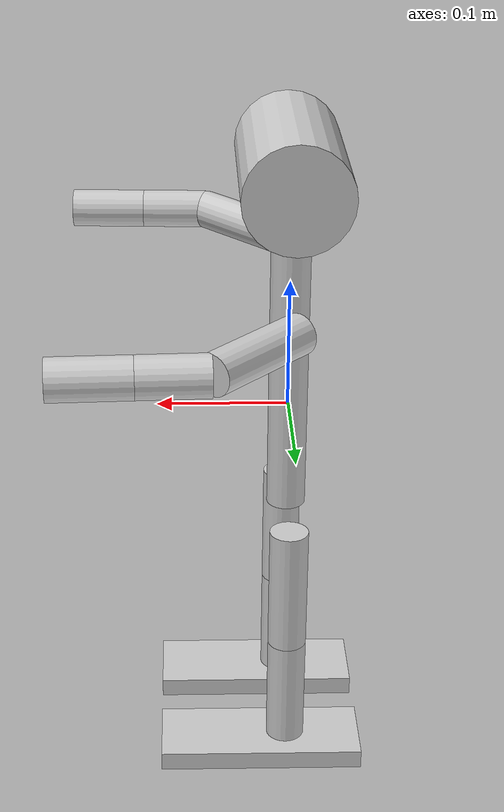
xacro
<?xml version="1.0" ?>
<robot name="NaoH25V32" xmlns:xacro="http://www.ros.org/wiki/xacro">
	<xacro:include filename="nao_visual_collisions.xacro"/>
	<xacro:include filename="nao_head.xacro"/>
	<xacro:include filename="nao_legs.xacro"/>
	<xacro:include filename="nao_torso.xacro"/>
	<xacro:include filename="nao_arms.xacro"/>
	<xacro:include filename="nao_sensors.xacro"/>
	<xacro:include filename="nao_fingers.xacro"/>
	<xacro:include filename="naoGazebo.xacro"/>
	<xacro:include filename="naoTransmission.xacro"/>
</robot>

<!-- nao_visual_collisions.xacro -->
<robot xmlns:xacro="http://www.ros.org/wiki/xacro">
	<xacro:property name="PI_2" value="1.57079632679"/>
	<xacro:property name="meshes_installed" value="false"/>
	<xacro:macro name="insert_visu_RFinger23_link">
		<xacro:unless value="${meshes_installed}"/>
		<xacro:if value="${meshes_installed}">
			<visual>
				<geometry>
					<mesh filename="package://nao_meshes/meshes/V32/RFinger23.dae" scale="0.1 0.1 0.1"/>
				</geometry>
				<origin rpy="0 0 0" xyz="0 0 0"/>
			</visual>
			<collision>
				<geometry>
					<mesh filename="package://nao_meshes/meshes/V32/RFinger23_0.10.stl" scale="0.1 0.1 0.1"/>
				</geometry>
				<origin rpy="0 0 0" xyz="0 0 0"/>
			</collision>
		</xacro:if>
	</xacro:macro>
	<xacro:macro name="insert_visu_LThigh">
		<xacro:unless value="${meshes_installed}">
			<visual>
				<geometry>
					<cylinder length="0.1" radius="0.015"/>
				</geometry>
				<origin rpy="0 0 0" xyz="0 0 -0.05"/>
				<material name="LightGrey"/>
			</visual>
			<collision>
				<geometry>
					<cylinder length="0.1" radius="0.015"/>
				</geometry>
				<origin rpy="0 0 0" xyz="0 0 -0.05"/>
			</collision>
		</xacro:unless>
		<xacro:if value="${meshes_installed}">
			<visual>
				<geometry>
					<mesh filename="package://nao_meshes/meshes/V32/LHipPitch.dae" scale="0.1 0.1 0.1"/>
				</geometry>
				<origin rpy="0 0 0" xyz="0 0 0"/>
			</visual>
			<collision>
				<geometry>
					<mesh filename="package://nao_meshes/meshes/V32/LHipPitch_0.10.stl" scale="0.1 0.1 0.1"/>
				</geometry>
				<origin rpy="0 0 0" xyz="0 0 0"/>
			</collision>
		</xacro:if>
	</xacro:macro>
	<xacro:macro name="insert_visu_RFinger13_link">
		<xacro:unless value="${meshes_installed}"/>
		<xacro:if value="${meshes_installed}">
			<visual>
				<geometry>
					<mesh filename="package://nao_meshes/meshes/V32/RFinger13.dae" scale="0.1 0.1 0.1"/>
				</geometry>
				<origin rpy="0 0 0" xyz="0 0 0"/>
			</visual>
			<collision>
				<geometry>
					<mesh filename="package://nao_meshes/meshes/V32/RFinger13_0.10.stl" scale="0.1 0.1 0.1"/>
				</geometry>
				<origin rpy="0 0 0" xyz="0 0 0"/>
			</collision>
		</xacro:if>
	</xacro:macro>
	<xacro:macro name="insert_visu_RThigh">
		<xacro:unless value="${meshes_installed}">
			<visual>
				<geometry>
					<cylinder length="0.1" radius="0.015"/>
				</geometry>
				<origin rpy="0 0 0" xyz="0 0 -0.05"/>
				<material name="LightGrey"/>
			</visual>
			<collision>
				<geometry>
					<cylinder length="0.1" radius="0.015"/>
				</geometry>
				<origin rpy="0 0 0" xyz="0 0 -0.05"/>
			</collision>
		</xacro:unless>
		<xacro:if value="${meshes_installed}">
			<visual>
				<geometry>
					<mesh filename="package://nao_meshes/meshes/V32/RHipPitch.dae" scale="0.1 0.1 0.1"/>
				</geometry>
				<origin rpy="0 0 0" xyz="0 0 0"/>
			</visual>
			<collision>
				<geometry>
					<mesh filename="package://nao_meshes/meshes/V32/RHipPitch_0.10.stl" scale="0.1 0.1 0.1"/>
				</geometry>
				<origin rpy="0 0 0" xyz="0 0 0"/>
			</collision>
		</xacro:if>
	</xacro:macro>
	<xacro:macro name="insert_visu_RFinger12_link">
		<xacro:unless value="${meshes_installed}"/>
		<xacro:if value="${meshes_installed}">
			<visual>
				<geometry>
					<mesh filename="package://nao_meshes/meshes/V32/RFinger12.dae" scale="0.1 0.1 0.1"/>
				</geometry>
				<origin rpy="0 0 0" xyz="0 0 0"/>
			</visual>
			<collision>
				<geometry>
					<mesh filename="package://nao_meshes/meshes/V32/RFinger12_0.10.stl" scale="0.1 0.1 0.1"/>
				</geometry>
				<origin rpy="0 0 0" xyz="0 0 0"/>
			</collision>
		</xacro:if>
	</xacro:macro>
	<xacro:macro name="insert_visu_LFinger21_link">
		<xacro:unless value="${meshes_installed}"/>
		<xacro:if value="${meshes_installed}">
			<visual>
				<geometry>
					<mesh filename="package://nao_meshes/meshes/V32/LFinger21.dae" scale="0.1 0.1 0.1"/>
				</geometry>
				<origin rpy="0 0 0" xyz="0 0 0"/>
			</visual>
			<collision>
				<geometry>
					<mesh filename="package://nao_meshes/meshes/V32/LFinger21_0.10.stl" scale="0.1 0.1 0.1"/>
				</geometry>
				<origin rpy="0 0 0" xyz="0 0 0"/>
			</collision>
		</xacro:if>
	</xacro:macro>
	<xacro:macro name="insert_visu_LFinger13_link">
		<xacro:unless value="${meshes_installed}"/>
		<xacro:if value="${meshes_installed}">
			<visual>
				<geometry>
					<mesh filename="package://nao_meshes/meshes/V32/LFinger13.dae" scale="0.1 0.1 0.1"/>
				</geometry>
				<origin rpy="0 0 0" xyz="0 0 0"/>
			</visual>
			<collision>
				<geometry>
					<mesh filename="package://nao_meshes/meshes/V32/LFinger13_0.10.stl" scale="0.1 0.1 0.1"/>
				</geometry>
				<origin rpy="0 0 0" xyz="0 0 0"/>
			</collision>
		</xacro:if>
	</xacro:macro>
	<xacro:macro name="insert_visu_LThumb1_link">
		<xacro:unless value="${meshes_installed}"/>
		<xacro:if value="${meshes_installed}">
			<visual>
				<geometry>
					<mesh filename="package://nao_meshes/meshes/V32/LThumb1.dae" scale="0.1 0.1 0.1"/>
				</geometry>
				<origin rpy="0 0 0" xyz="0 0 0"/>
			</visual>
			<collision>
				<geometry>
					<mesh filename="package://nao_meshes/meshes/V32/LThumb1_0.10.stl" scale="0.1 0.1 0.1"/>
				</geometry>
				<origin rpy="0 0 0" xyz="0 0 0"/>
			</collision>
		</xacro:if>
	</xacro:macro>
	<xacro:macro name="insert_visu_LFinger11_link">
		<xacro:unless value="${meshes_installed}"/>
		<xacro:if value="${meshes_installed}">
			<visual>
				<geometry>
					<mesh filename="package://nao_meshes/meshes/V32/LFinger11.dae" scale="0.1 0.1 0.1"/>
				</geometry>
				<origin rpy="0 0 0" xyz="0 0 0"/>
			</visual>
			<collision>
				<geometry>
					<mesh filename="package://nao_meshes/meshes/V32/LFinger11_0.10.stl" scale="0.1 0.1 0.1"/>
				</geometry>
				<origin rpy="0 0 0" xyz="0 0 0"/>
			</collision>
		</xacro:if>
	</xacro:macro>
	<xacro:macro name="insert_visu_RFinger22_link">
		<xacro:unless value="${meshes_installed}"/>
		<xacro:if value="${meshes_installed}">
			<visual>
				<geometry>
					<mesh filename="package://nao_meshes/meshes/V32/RFinger22.dae" scale="0.1 0.1 0.1"/>
				</geometry>
				<origin rpy="0 0 0" xyz="0 0 0"/>
			</visual>
			<collision>
				<geometry>
					<mesh filename="package://nao_meshes/meshes/V32/RFinger22_0.10.stl" scale="0.1 0.1 0.1"/>
				</geometry>
				<origin rpy="0 0 0" xyz="0 0 0"/>
			</collision>
		</xacro:if>
	</xacro:macro>
	<xacro:macro name="insert_visu_Head">
		<xacro:unless value="${meshes_installed}">
			<visual>
				<geometry>
					<cylinder length="0.14" radius="0.04"/>
				</geometry>
				<origin rpy="1.57079632679 0 0" xyz="0 0 0.058"/>
				<material name="LightGrey"/>
			</visual>
			<collision>
				<geometry>
					<cylinder length="0.14" radius="0.04"/>
				</geometry>
				<origin rpy="1.57079632679 0 0" xyz="0 0 0.058"/>
			</collision>
		</xacro:unless>
		<xacro:if value="${meshes_installed}">
			<visual>
				<geometry>
					<mesh filename="package://nao_meshes/meshes/V32/HeadPitch.dae" scale="0.1 0.1 0.1"/>
				</geometry>
				<origin rpy="0 0 0" xyz="0 0 0"/>
			</visual>
			<collision>
				<geometry>
					<mesh filename="package://nao_meshes/meshes/V32/HeadPitch_0.10.stl" scale="0.1 0.1 0.1"/>
				</geometry>
				<origin rpy="0 0 0" xyz="0 0 0"/>
			</collision>
		</xacro:if>
	</xacro:macro>
	<xacro:macro name="insert_visu_LFinger22_link">
		<xacro:unless value="${meshes_installed}"/>
		<xacro:if value="${meshes_installed}">
			<visual>
				<geometry>
					<mesh filename="package://nao_meshes/meshes/V32/LFinger22.dae" scale="0.1 0.1 0.1"/>
				</geometry>
				<origin rpy="0 0 0" xyz="0 0 0"/>
			</visual>
			<collision>
				<geometry>
					<mesh filename="package://nao_meshes/meshes/V32/LFinger22_0.10.stl" scale="0.1 0.1 0.1"/>
				</geometry>
				<origin rpy="0 0 0" xyz="0 0 0"/>
			</collision>
		</xacro:if>
	</xacro:macro>
	<xacro:macro name="insert_visu_RFinger21_link">
		<xacro:unless value="${meshes_installed}"/>
		<xacro:if value="${meshes_installed}">
			<visual>
				<geometry>
					<mesh filename="package://nao_meshes/meshes/V32/RFinger21.dae" scale="0.1 0.1 0.1"/>
				</geometry>
				<origin rpy="0 0 0" xyz="0 0 0"/>
			</visual>
			<collision>
				<geometry>
					<mesh filename="package://nao_meshes/meshes/V32/RFinger21_0.10.stl" scale="0.1 0.1 0.1"/>
				</geometry>
				<origin rpy="0 0 0" xyz="0 0 0"/>
			</collision>
		</xacro:if>
	</xacro:macro>
	<xacro:macro name="insert_visu_LBicep">
		<xacro:unless value="${meshes_installed}">
			<visual>
				<geometry>
					<cylinder length="0.09" radius="0.015"/>
				</geometry>
				<origin rpy="1.57079632679 0 1.57079632679" xyz="0.045 0 0"/>
				<material name="LightGrey"/>
			</visual>
			<collision>
				<geometry>
					<cylinder length="0.09" radius="0.015"/>
				</geometry>
				<origin rpy="1.57079632679 0 1.57079632679" xyz="0.045 0 0"/>
			</collision>
		</xacro:unless>
		<xacro:if value="${meshes_installed}">
			<visual>
				<geometry>
					<mesh filename="package://nao_meshes/meshes/V32/LShoulderRoll.dae" scale="0.1 0.1 0.1"/>
				</geometry>
				<origin rpy="0 0 0" xyz="0 0 0"/>
			</visual>
			<collision>
				<geometry>
					<mesh filename="package://nao_meshes/meshes/V32/LShoulderRoll_0.10.stl" scale="0.1 0.1 0.1"/>
				</geometry>
				<origin rpy="0 0 0" xyz="0 0 0"/>
			</collision>
		</xacro:if>
	</xacro:macro>
	<xacro:macro name="insert_visu_RThumb1_link">
		<xacro:unless value="${meshes_installed}"/>
		<xacro:if value="${meshes_installed}">
			<visual>
				<geometry>
					<mesh filename="package://nao_meshes/meshes/V32/RThumb1.dae" scale="0.1 0.1 0.1"/>
				</geometry>
				<origin rpy="0 0 0" xyz="0 0 0"/>
			</visual>
			<collision>
				<geometry>
					<mesh filename="package://nao_meshes/meshes/V32/RThumb1_0.10.stl" scale="0.1 0.1 0.1"/>
				</geometry>
				<origin rpy="0 0 0" xyz="0 0 0"/>
			</collision>
		</xacro:if>
	</xacro:macro>
	<xacro:macro name="insert_visu_RThumb2_link">
		<xacro:unless value="${meshes_installed}"/>
		<xacro:if value="${meshes_installed}">
			<visual>
				<geometry>
					<mesh filename="package://nao_meshes/meshes/V32/RThumb2.dae" scale="0.1 0.1 0.1"/>
				</geometry>
				<origin rpy="0 0 0" xyz="0 0 0"/>
			</visual>
			<collision>
				<geometry>
					<mesh filename="package://nao_meshes/meshes/V32/RThumb2_0.10.stl" scale="0.1 0.1 0.1"/>
				</geometry>
				<origin rpy="0 0 0" xyz="0 0 0"/>
			</collision>
		</xacro:if>
	</xacro:macro>
	<xacro:macro name="insert_visu_r_wrist">
		<xacro:unless value="${meshes_installed}">
			<visual>
				<geometry>
					<cylinder length="0.058" radius="0.015"/>
				</geometry>
				<origin rpy="1.57079632679 0 1.57079632679" xyz="0.029 0 0"/>
				<material name="LightGrey"/>
			</visual>
			<collision>
				<geometry>
					<cylinder length="0.058" radius="0.015"/>
				</geometry>
				<origin rpy="1.57079632679 0 1.57079632679" xyz="0.029 0 0"/>
			</collision>
		</xacro:unless>
		<xacro:if value="${meshes_installed}">
			<visual>
				<geometry>
					<mesh filename="package://nao_meshes/meshes/V32/RWristYaw.dae" scale="0.1 0.1 0.1"/>
				</geometry>
				<origin rpy="0 0 0" xyz="0 0 0"/>
			</visual>
			<collision>
				<geometry>
					<mesh filename="package://nao_meshes/meshes/V32/RWristYaw_0.10.stl" scale="0.1 0.1 0.1"/>
				</geometry>
				<origin rpy="0 0 0" xyz="0 0 0"/>
			</collision>
		</xacro:if>
	</xacro:macro>
	<xacro:macro name="insert_visu_LForeArm">
		<xacro:unless value="${meshes_installed}">
			<visual>
				<geometry>
					<cylinder length="0.05065" radius="0.015"/>
				</geometry>
				<origin rpy="1.57079632679 0 1.57079632679" xyz="0.025325 0 0"/>
				<material name="LightGrey"/>
			</visual>
			<collision>
				<geometry>
					<cylinder length="0.05065" radius="0.015"/>
				</geometry>
				<origin rpy="1.57079632679 0 1.57079632679" xyz="0.025325 0 0"/>
			</collision>
		</xacro:unless>
		<xacro:if value="${meshes_installed}">
			<visual>
				<geometry>
					<mesh filename="package://nao_meshes/meshes/V32/LElbowRoll.dae" scale="0.1 0.1 0.1"/>
				</geometry>
				<origin rpy="0 0 0" xyz="0 0 0"/>
			</visual>
			<collision>
				<geometry>
					<mesh filename="package://nao_meshes/meshes/V32/LElbowRoll_0.10.stl" scale="0.1 0.1 0.1"/>
				</geometry>
				<origin rpy="0 0 0" xyz="0 0 0"/>
			</collision>
		</xacro:if>
	</xacro:macro>
	<xacro:macro name="insert_visu_RHip">
		<xacro:unless value="${meshes_installed}"/>
		<xacro:if value="${meshes_installed}">
			<visual>
				<geometry>
					<mesh filename="package://nao_meshes/meshes/V32/RHipRoll.dae" scale="0.1 0.1 0.1"/>
				</geometry>
				<origin rpy="0 0 0" xyz="0 0 0"/>
			</visual>
			<collision>
				<geometry>
					<mesh filename="package://nao_meshes/meshes/V32/RHipRoll_0.10.stl" scale="0.1 0.1 0.1"/>
				</geometry>
				<origin rpy="0 0 0" xyz="0 0 0"/>
			</collision>
		</xacro:if>
	</xacro:macro>
	<xacro:macro name="insert_visu_LThumb2_link">
		<xacro:unless value="${meshes_installed}"/>
		<xacro:if value="${meshes_installed}">
			<visual>
				<geometry>
					<mesh filename="package://nao_meshes/meshes/V32/LThumb2.dae" scale="0.1 0.1 0.1"/>
				</geometry>
				<origin rpy="0 0 0" xyz="0 0 0"/>
			</visual>
			<collision>
				<geometry>
					<mesh filename="package://nao_meshes/meshes/V32/LThumb2_0.10.stl" scale="0.1 0.1 0.1"/>
				</geometry>
				<origin rpy="0 0 0" xyz="0 0 0"/>
			</collision>
		</xacro:if>
	</xacro:macro>
	<xacro:macro name="insert_visu_LFinger12_link">
		<xacro:unless value="${meshes_installed}"/>
		<xacro:if value="${meshes_installed}">
			<visual>
				<geometry>
					<mesh filename="package://nao_meshes/meshes/V32/LFinger12.dae" scale="0.1 0.1 0.1"/>
				</geometry>
				<origin rpy="0 0 0" xyz="0 0 0"/>
			</visual>
			<collision>
				<geometry>
					<mesh filename="package://nao_meshes/meshes/V32/LFinger12_0.10.stl" scale="0.1 0.1 0.1"/>
				</geometry>
				<origin rpy="0 0 0" xyz="0 0 0"/>
			</collision>
		</xacro:if>
	</xacro:macro>
	<xacro:macro name="insert_visu_RTibia">
		<xacro:unless value="${meshes_installed}">
			<visual>
				<geometry>
					<cylinder length="0.1" radius="0.015"/>
				</geometry>
				<origin rpy="0 0 0" xyz="0 0 -0.05"/>
				<material name="LightGrey"/>
			</visual>
			<collision>
				<geometry>
					<cylinder length="0.1" radius="0.015"/>
				</geometry>
				<origin rpy="0 0 0" xyz="0 0 -0.05"/>
			</collision>
		</xacro:unless>
		<xacro:if value="${meshes_installed}">
			<visual>
				<geometry>
					<mesh filename="package://nao_meshes/meshes/V32/RKneePitch.dae" scale="0.1 0.1 0.1"/>
				</geometry>
				<origin rpy="0 0 0" xyz="0 0 0"/>
			</visual>
			<collision>
				<geometry>
					<mesh filename="package://nao_meshes/meshes/V32/RKneePitch_0.10.stl" scale="0.1 0.1 0.1"/>
				</geometry>
				<origin rpy="0 0 0" xyz="0 0 0"/>
			</collision>
		</xacro:if>
	</xacro:macro>
	<xacro:macro name="insert_visu_RShoulder">
		<xacro:unless value="${meshes_installed}"/>
		<xacro:if value="${meshes_installed}">
			<visual>
				<geometry>
					<mesh filename="package://nao_meshes/meshes/V32/RShoulderPitch.dae" scale="0.1 0.1 0.1"/>
				</geometry>
				<origin rpy="0 0 0" xyz="0 0 0"/>
			</visual>
			<collision>
				<geometry>
					<mesh filename="package://nao_meshes/meshes/V32/RShoulderPitch_0.10.stl" scale="0.1 0.1 0.1"/>
				</geometry>
				<origin rpy="0 0 0" xyz="0 0 0"/>
			</collision>
		</xacro:if>
	</xacro:macro>
	<xacro:macro name="insert_visu_LHip">
		<xacro:unless value="${meshes_installed}"/>
		<xacro:if value="${meshes_installed}">
			<visual>
				<geometry>
					<mesh filename="package://nao_meshes/meshes/V32/LHipRoll.dae" scale="0.1 0.1 0.1"/>
				</geometry>
				<origin rpy="0 0 0" xyz="0 0 0"/>
			</visual>
			<collision>
				<geometry>
					<mesh filename="package://nao_meshes/meshes/V32/LHipRoll_0.10.stl" scale="0.1 0.1 0.1"/>
				</geometry>
				<origin rpy="0 0 0" xyz="0 0 0"/>
			</collision>
		</xacro:if>
	</xacro:macro>
	<xacro:macro name="insert_visu_l_wrist">
		<xacro:unless value="${meshes_installed}">
			<visual>
				<geometry>
					<cylinder length="0.058" radius="0.015"/>
				</geometry>
				<origin rpy="1.57079632679 0 1.57079632679" xyz="0.029 0 0"/>
				<material name="LightGrey"/>
			</visual>
			<collision>
				<geometry>
					<cylinder length="0.058" radius="0.015"/>
				</geometry>
				<origin rpy="1.57079632679 0 1.57079632679" xyz="0.029 0 0"/>
			</collision>
		</xacro:unless>
		<xacro:if value="${meshes_installed}">
			<visual>
				<geometry>
					<mesh filename="package://nao_meshes/meshes/V32/LWristYaw.dae" scale="0.1 0.1 0.1"/>
				</geometry>
				<origin rpy="0 0 0" xyz="0 0 0"/>
			</visual>
			<collision>
				<geometry>
					<mesh filename="package://nao_meshes/meshes/V32/LWristYaw_0.10.stl" scale="0.1 0.1 0.1"/>
				</geometry>
				<origin rpy="0 0 0" xyz="0 0 0"/>
			</collision>
		</xacro:if>
	</xacro:macro>
	<xacro:macro name="insert_visu_RBicep">
		<xacro:unless value="${meshes_installed}">
			<visual>
				<geometry>
					<cylinder length="0.09" radius="0.015"/>
				</geometry>
				<origin rpy="1.57079632679 0 1.57079632679" xyz="0.045 0 0"/>
				<material name="LightGrey"/>
			</visual>
			<collision>
				<geometry>
					<cylinder length="0.09" radius="0.015"/>
				</geometry>
				<origin rpy="1.57079632679 0 1.57079632679" xyz="0.045 0 0"/>
			</collision>
		</xacro:unless>
		<xacro:if value="${meshes_installed}">
			<visual>
				<geometry>
					<mesh filename="package://nao_meshes/meshes/V32/RShoulderRoll.dae" scale="0.1 0.1 0.1"/>
				</geometry>
				<origin rpy="0 0 0" xyz="0 0 0"/>
			</visual>
			<collision>
				<geometry>
					<mesh filename="package://nao_meshes/meshes/V32/RShoulderRoll_0.10.stl" scale="0.1 0.1 0.1"/>
				</geometry>
				<origin rpy="0 0 0" xyz="0 0 0"/>
			</collision>
		</xacro:if>
	</xacro:macro>
	<xacro:macro name="insert_visu_RFinger11_link">
		<xacro:unless value="${meshes_installed}"/>
		<xacro:if value="${meshes_installed}">
			<visual>
				<geometry>
					<mesh filename="package://nao_meshes/meshes/V32/RFinger11.dae" scale="0.1 0.1 0.1"/>
				</geometry>
				<origin rpy="0 0 0" xyz="0 0 0"/>
			</visual>
			<collision>
				<geometry>
					<mesh filename="package://nao_meshes/meshes/V32/RFinger11_0.10.stl" scale="0.1 0.1 0.1"/>
				</geometry>
				<origin rpy="0 0 0" xyz="0 0 0"/>
			</collision>
		</xacro:if>
	</xacro:macro>
	<xacro:macro name="insert_visu_LFinger23_link">
		<xacro:unless value="${meshes_installed}"/>
		<xacro:if value="${meshes_installed}">
			<visual>
				<geometry>
					<mesh filename="package://nao_meshes/meshes/V32/LFinger23.dae" scale="0.1 0.1 0.1"/>
				</geometry>
				<origin rpy="0 0 0" xyz="0 0 0"/>
			</visual>
			<collision>
				<geometry>
					<mesh filename="package://nao_meshes/meshes/V32/LFinger23_0.10.stl" scale="0.1 0.1 0.1"/>
				</geometry>
				<origin rpy="0 0 0" xyz="0 0 0"/>
			</collision>
		</xacro:if>
	</xacro:macro>
	<xacro:macro name="insert_visu_LTibia">
		<xacro:unless value="${meshes_installed}">
			<visual>
				<geometry>
					<cylinder length="0.1" radius="0.015"/>
				</geometry>
				<origin rpy="0 0 0" xyz="0 0 -0.05"/>
				<material name="LightGrey"/>
			</visual>
			<collision>
				<geometry>
					<cylinder length="0.1" radius="0.015"/>
				</geometry>
				<origin rpy="0 0 0" xyz="0 0 -0.05"/>
			</collision>
		</xacro:unless>
		<xacro:if value="${meshes_installed}">
			<visual>
				<geometry>
					<mesh filename="package://nao_meshes/meshes/V32/LKneePitch.dae" scale="0.1 0.1 0.1"/>
				</geometry>
				<origin rpy="0 0 0" xyz="0 0 0"/>
			</visual>
			<collision>
				<geometry>
					<mesh filename="package://nao_meshes/meshes/V32/LKneePitch_0.10.stl" scale="0.1 0.1 0.1"/>
				</geometry>
				<origin rpy="0 0 0" xyz="0 0 0"/>
			</collision>
		</xacro:if>
	</xacro:macro>
	<xacro:macro name="insert_visu_Neck">
		<xacro:unless value="${meshes_installed}"/>
		<xacro:if value="${meshes_installed}">
			<visual>
				<geometry>
					<mesh filename="package://nao_meshes/meshes/V32/HeadYaw.dae" scale="0.1 0.1 0.1"/>
				</geometry>
				<origin rpy="0 0 0" xyz="0 0 0"/>
			</visual>
			<collision>
				<geometry>
					<mesh filename="package://nao_meshes/meshes/V32/HeadYaw_0.10.stl" scale="0.1 0.1 0.1"/>
				</geometry>
				<origin rpy="0 0 0" xyz="0 0 0"/>
			</collision>
		</xacro:if>
	</xacro:macro>
	<xacro:macro name="insert_visu_LAnklePitch">
		<xacro:unless value="${meshes_installed}"/>
		<xacro:if value="${meshes_installed}">
			<visual>
				<geometry>
					<mesh filename="package://nao_meshes/meshes/V32/LAnklePitch.dae" scale="0.1 0.1 0.1"/>
				</geometry>
				<origin rpy="0 0 0" xyz="0 0 0"/>
			</visual>
			<collision>
				<geometry>
					<mesh filename="package://nao_meshes/meshes/V32/LAnklePitch_0.10.stl" scale="0.1 0.1 0.1"/>
				</geometry>
				<origin rpy="0 0 0" xyz="0 0 0"/>
			</collision>
		</xacro:if>
	</xacro:macro>
	<xacro:macro name="insert_visu_RPelvis">
		<xacro:unless value="${meshes_installed}"/>
		<xacro:if value="${meshes_installed}">
			<visual>
				<geometry>
					<mesh filename="package://nao_meshes/meshes/V32/RHipYawPitch.dae" scale="0.1 0.1 0.1"/>
				</geometry>
				<origin rpy="0 0 0" xyz="0 0 0"/>
			</visual>
			<collision>
				<geometry>
					<mesh filename="package://nao_meshes/meshes/V32/RHipYawPitch_0.10.stl" scale="0.1 0.1 0.1"/>
				</geometry>
				<origin rpy="0 0 0" xyz="0 0 0"/>
			</collision>
		</xacro:if>
	</xacro:macro>
	<xacro:macro name="insert_visu_RAnklePitch">
		<xacro:unless value="${meshes_installed}"/>
		<xacro:if value="${meshes_installed}">
			<visual>
				<geometry>
					<mesh filename="package://nao_meshes/meshes/V32/RAnklePitch.dae" scale="0.1 0.1 0.1"/>
				</geometry>
				<origin rpy="0 0 0" xyz="0 0 0"/>
			</visual>
			<collision>
				<geometry>
					<mesh filename="package://nao_meshes/meshes/V32/RAnklePitch_0.10.stl" scale="0.1 0.1 0.1"/>
				</geometry>
				<origin rpy="0 0 0" xyz="0 0 0"/>
			</collision>
		</xacro:if>
	</xacro:macro>
	<xacro:macro name="insert_visu_torso">
		<xacro:unless value="${meshes_installed}">
			<visual>
				<geometry>
					<cylinder length="0.2115" radius="0.015"/>
				</geometry>
				<origin rpy="0 0 0" xyz="0 0 0.02075"/>
				<material name="LightGrey"/>
			</visual>
			<collision>
				<geometry>
					<cylinder length="0.2115" radius="0.015"/>
				</geometry>
				<origin rpy="0 0 0" xyz="0 0 0.02075"/>
			</collision>
		</xacro:unless>
		<xacro:if value="${meshes_installed}">
			<visual>
				<geometry>
					<mesh filename="package://nao_meshes/meshes/V32/Torso.dae" scale="0.1 0.1 0.1"/>
				</geometry>
				<origin rpy="0 0 0" xyz="0 0 0"/>
			</visual>
			<collision>
				<geometry>
					<mesh filename="package://nao_meshes/meshes/V32/Torso_0.10.stl" scale="0.1 0.1 0.1"/>
				</geometry>
				<origin rpy="0 0 0" xyz="0 0 0"/>
			</collision>
		</xacro:if>
	</xacro:macro>
	<xacro:macro name="insert_visu_r_ankle">
		<xacro:unless value="${meshes_installed}">
			<visual>
				<geometry>
					<box size="0.16 0.06 0.015"/>
				</geometry>
				<origin rpy="0 0 0" xyz="0.02 0 0.0075"/>
				<material name="LightGrey"/>
			</visual>
			<collision>
				<geometry>
					<box size="0.16 0.06 0.015"/>
				</geometry>
				<origin rpy="0 0 0" xyz="0.02 0 0.0075"/>
			</collision>
		</xacro:unless>
		<xacro:if value="${meshes_installed}">
			<visual>
				<geometry>
					<mesh filename="package://nao_meshes/meshes/V32/RAnkleRoll.dae" scale="0.1 0.1 0.1"/>
				</geometry>
				<origin rpy="0 0 0" xyz="0 0 0"/>
			</visual>
			<collision>
				<geometry>
					<mesh filename="package://nao_meshes/meshes/V32/RAnkleRoll_0.10.stl" scale="0.1 0.1 0.1"/>
				</geometry>
				<origin rpy="0 0 0" xyz="0 0 0"/>
			</collision>
		</xacro:if>
	</xacro:macro>
	<xacro:macro name="insert_visu_l_ankle">
		<xacro:unless value="${meshes_installed}">
			<visual>
				<geometry>
					<box size="0.16 0.06 0.015"/>
				</geometry>
				<origin rpy="0 0 0" xyz="0.02 0 0.0075"/>
				<material name="LightGrey"/>
			</visual>
			<collision>
				<geometry>
					<box size="0.16 0.06 0.015"/>
				</geometry>
				<origin rpy="0 0 0" xyz="0.02 0 0.0075"/>
			</collision>
		</xacro:unless>
		<xacro:if value="${meshes_installed}">
			<visual>
				<geometry>
					<mesh filename="package://nao_meshes/meshes/V32/LAnkleRoll.dae" scale="0.1 0.1 0.1"/>
				</geometry>
				<origin rpy="0 0 0" xyz="0 0 0"/>
			</visual>
			<collision>
				<geometry>
					<mesh filename="package://nao_meshes/meshes/V32/LAnkleRoll_0.10.stl" scale="0.1 0.1 0.1"/>
				</geometry>
				<origin rpy="0 0 0" xyz="0 0 0"/>
			</collision>
		</xacro:if>
	</xacro:macro>
	<xacro:macro name="insert_visu_RForeArm">
		<xacro:unless value="${meshes_installed}">
			<visual>
				<geometry>
					<cylinder length="0.05065" radius="0.015"/>
				</geometry>
				<origin rpy="1.57079632679 0 1.57079632679" xyz="0.025325 0 0"/>
				<material name="LightGrey"/>
			</visual>
			<collision>
				<geometry>
					<cylinder length="0.05065" radius="0.015"/>
				</geometry>
				<origin rpy="1.57079632679 0 1.57079632679" xyz="0.025325 0 0"/>
			</collision>
		</xacro:unless>
		<xacro:if value="${meshes_installed}">
			<visual>
				<geometry>
					<mesh filename="package://nao_meshes/meshes/V32/RElbowRoll.dae" scale="0.1 0.1 0.1"/>
				</geometry>
				<origin rpy="0 0 0" xyz="0 0 0"/>
			</visual>
			<collision>
				<geometry>
					<mesh filename="package://nao_meshes/meshes/V32/RElbowRoll_0.10.stl" scale="0.1 0.1 0.1"/>
				</geometry>
				<origin rpy="0 0 0" xyz="0 0 0"/>
			</collision>
		</xacro:if>
	</xacro:macro>
	<xacro:macro name="insert_visu_LShoulder">
		<xacro:unless value="${meshes_installed}"/>
		<xacro:if value="${meshes_installed}">
			<visual>
				<geometry>
					<mesh filename="package://nao_meshes/meshes/V32/LShoulderPitch.dae" scale="0.1 0.1 0.1"/>
				</geometry>
				<origin rpy="0 0 0" xyz="0 0 0"/>
			</visual>
			<collision>
				<geometry>
					<mesh filename="package://nao_meshes/meshes/V32/LShoulderPitch_0.10.stl" scale="0.1 0.1 0.1"/>
				</geometry>
				<origin rpy="0 0 0" xyz="0 0 0"/>
			</collision>
		</xacro:if>
	</xacro:macro>
	<xacro:macro name="insert_visu_LPelvis">
		<xacro:unless value="${meshes_installed}"/>
		<xacro:if value="${meshes_installed}">
			<visual>
				<geometry>
					<mesh filename="package://nao_meshes/meshes/V32/LHipYawPitch.dae" scale="0.1 0.1 0.1"/>
				</geometry>
				<origin rpy="0 0 0" xyz="0 0 0"/>
			</visual>
			<collision>
				<geometry>
					<mesh filename="package://nao_meshes/meshes/V32/LHipYawPitch_0.10.stl" scale="0.1 0.1 0.1"/>
				</geometry>
				<origin rpy="0 0 0" xyz="0 0 0"/>
			</collision>
		</xacro:if>
	</xacro:macro>
</robot>

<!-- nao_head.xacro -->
<robot xmlns:xacro="http://www.ros.org/wiki/xacro">
	<joint name="HeadYaw" type="revolute">
		<parent link="torso"/>
		<child link="Neck"/>
		<origin rpy="0 0 0" xyz="0 0 0.1265"/>
		<axis xyz="0 0 1.0"/>
		<limit effort="1.547" lower="-2.08567" upper="2.08567" velocity="8.26797"/>
	</joint>
	<link name="Neck">
		<inertial>
			<mass value="0.05959"/>
			<inertia ixx="2.27831e-05" ixy="0" ixz="-2.84825e-08" iyy="2.37937e-05" iyz="-1.0416e-07" izz="5.49457e-06"/>
			<origin rpy="0 0 0" xyz="-3e-05 0 -0.02573"/>
		</inertial>
		<xacro:insert_visu_Neck/>
	</link>
	<joint name="HeadPitch" type="revolute">
		<parent link="Neck"/>
		<child link="Head"/>
		<origin rpy="0 0 0" xyz="0 0 0"/>
		<axis xyz="0 1.0 0"/>
		<limit effort="1.532" lower="-0.671952" upper="0.514872" velocity="7.19407"/>
	</joint>
	<link name="Head">
		<inertial>
			<mass value="0.47672"/>
			<inertia ixx="0.0036122" ixy="1.42859e-05" ixz="0.000289597" iyy="0.00342929" iyz="-2.22459e-05" izz="0.00156014"/>
			<origin rpy="0 0 0" xyz="0.00383 0 0.05156"/>
		</inertial>
		<xacro:insert_visu_Head/>
	</link>
	<joint name="gaze_joint" type="fixed">
		<parent link="Head"/>
		<child link="gaze"/>
		<origin rpy="0 0 0" xyz="0.05871 0 0.06364"/>
	</joint>
	<link name="gaze"/>
</robot>

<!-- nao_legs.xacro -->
<robot xmlns:xacro="http://www.ros.org/wiki/xacro">
	<joint name="LHipYawPitch" type="revolute">
		<parent link="torso"/>
		<child link="LPelvis"/>
		<origin rpy="0 0 0" xyz="0 0.05 -0.085"/>
		<axis xyz="0 0.707106 -0.707106"/>
		<limit effort="3.348" lower="-1.14529" upper="0.740718" velocity="4.16174"/>
	</joint>
	<link name="LPelvis">
		<inertial>
			<mass value="0.07244"/>
			<inertia ixx="2.74339e-05" ixy="1.27703e-06" ixz="-1.83038e-06" iyy="4.99292e-05" iyz="4.57891e-06" izz="5.3498e-05"/>
			<origin rpy="0 0 0" xyz="-0.00717 -0.01187 0.02705"/>
		</inertial>
		<xacro:insert_visu_LPelvis/>
	</link>
	<joint name="LHipRoll" type="revolute">
		<parent link="LPelvis"/>
		<child link="LHip"/>
		<origin rpy="0 0 0" xyz="0 0 0"/>
		<axis xyz="1.0 0 0"/>
		<limit effort="3.348" lower="-0.379435" upper="0.79046" velocity="4.16174"/>
	</joint>
	<link name="LHip">
		<inertial>
			<mass value="0.1353"/>
			<inertia ixx="2.4849e-05" ixy="-5.97198e-07" ixz="5.28803e-06" iyy="6.16256e-05" iyz="-1.85886e-07" izz="0.000255291"/>
			<origin rpy="0 0 0" xyz="-0.01649 0.00029 -0.00475"/>
		</inertial>
		<xacro:insert_visu_LHip/>
	</link>
	<joint name="LHipPitch" type="revolute">
		<parent link="LHip"/>
		<child link="LThigh"/>
		<origin rpy="0 0 0" xyz="0 0 0"/>
		<axis xyz="0 1.0 0"/>
		<limit effort="3.023" lower="-1.53589" upper="0.48398" velocity="6.40239"/>
	</joint>
	<link name="LThigh">
		<inertial>
			<mass value="0.39798"/>
			<inertia ixx="0.000509482" ixy="1.48043e-06" ixz="5.4425e-05" iyy="0.000469814" iyz="-1.13419e-05" izz="0.000302638"/>
			<origin rpy="0 0 0" xyz="0.00131 0.00201 -0.05386"/>
		</inertial>
		<xacro:insert_visu_LThigh/>
	</link>
	<joint name="LKneePitch" type="revolute">
		<parent link="LThigh"/>
		<child link="LTibia"/>
		<origin rpy="0 0 0" xyz="0 0 -0.1"/>
		<axis xyz="0 1.0 0"/>
		<limit effort="3.023" lower="-0.0923279" upper="2.11255" velocity="6.40239"/>
	</joint>
	<link name="LTibia">
		<inertial>
			<mass value="0.29714"/>
			<inertia ixx="0.000468213" ixy="3.24443e-06" ixz="-2.82799e-05" iyy="0.000411872" iyz="5.21684e-06" izz="0.000185588"/>
			<origin rpy="0 0 0" xyz="0.00471 0.0021 -0.04891"/>
		</inertial>
		<xacro:insert_visu_LTibia/>
	</link>
	<joint name="LAnklePitch" type="revolute">
		<parent link="LTibia"/>
		<child link="LAnklePitch"/>
		<origin rpy="0 0 0" xyz="0 0 -0.1029"/>
		<axis xyz="0 1.0 0"/>
		<limit effort="3.023" lower="-1.18944" upper="0.922581" velocity="6.40239"/>
	</joint>
	<link name="LAnklePitch">
		<inertial>
			<mass value="0.13892"/>
			<inertia ixx="3.31602e-05" ixy="5.81459e-09" ixz="3.47177e-06" iyy="6.6181e-05" iyz="2.54907e-07" izz="5.32289e-05"/>
			<origin rpy="0 0 0" xyz="0.00142 0.00028 0.00638"/>
		</inertial>
		<xacro:insert_visu_LAnklePitch/>
	</link>
	<joint name="LAnkleRoll" type="revolute">
		<parent link="LAnklePitch"/>
		<child link="l_ankle"/>
		<origin rpy="0 0 0" xyz="0 0 0"/>
		<axis xyz="1.0 0 0"/>
		<limit effort="3.348" lower="-0.397761" upper="0.768992" velocity="4.16174"/>
	</joint>
	<link name="l_ankle">
		<inertial>
			<mass value="0.16304"/>
			<inertia ixx="9.80337e-05" ixy="7.46444e-06" ixz="7.11645e-06" iyy="0.000374354" iyz="1.43763e-06" izz="0.000423717"/>
			<origin rpy="0 0 0" xyz="0.02489 0.0033 -0.03208"/>
		</inertial>
		<xacro:insert_visu_l_ankle/>
	</link>
	<joint name="LLeg_effector_fixedjoint" type="fixed">
		<parent link="l_ankle"/>
		<child link="l_sole"/>
		<origin rpy="0 0 0" xyz="0 0 -0.04511"/>
		<axis xyz="0 0 0"/>
	</joint>
	<link name="l_sole"/>
	<joint name="RHipYawPitch" type="revolute">
		<parent link="torso"/>
		<child link="RPelvis"/>
		<origin rpy="0 0 0" xyz="0 -0.05 -0.085"/>
		<axis xyz="0 0.707106 0.707106"/>
		<limit effort="3.348" lower="-1.14529" upper="0.740718" velocity="4.16174"/>
		<mimic joint="LHipYawPitch" multiplier="1.0" offset="0"/>
	</joint>
	<link name="RPelvis">
		<inertial>
			<mass value="0.07244"/>
			<inertia ixx="2.74339e-05" ixy="-1.27703e-06" ixz="-1.83038e-06" iyy="4.99292e-05" iyz="-4.57891e-06" izz="5.3498e-05"/>
			<origin rpy="0 0 0" xyz="-0.00717 0.01187 0.02705"/>
		</inertial>
		<xacro:insert_visu_RPelvis/>
	</link>
	<joint name="RHipRoll" type="revolute">
		<parent link="RPelvis"/>
		<child link="RHip"/>
		<origin rpy="0 0 0" xyz="0 0 0"/>
		<axis xyz="1.0 0 0"/>
		<limit effort="3.348" lower="-0.79046" upper="0.379435" velocity="4.16174"/>
	</joint>
	<link name="RHip">
		<inertial>
			<mass value="0.1353"/>
			<inertia ixx="2.4849e-05" ixy="5.97198e-07" ixz="5.28803e-06" iyy="6.16256e-05" iyz="1.85886e-07" izz="0.000255291"/>
			<origin rpy="0 0 0" xyz="-0.01649 -0.00029 -0.00475"/>
		</inertial>
		<xacro:insert_visu_RHip/>
	</link>
	<joint name="RHipPitch" type="revolute">
		<parent link="RHip"/>
		<child link="RThigh"/>
		<origin rpy="0 0 0" xyz="0 0 0"/>
		<axis xyz="0 1.0 0"/>
		<limit effort="3.0226" lower="-1.53589" upper="0.48398" velocity="6.40239"/>
	</joint>
	<link name="RThigh">
		<inertial>
			<mass value="0.39798"/>
			<inertia ixx="0.000509482" ixy="-1.48043e-06" ixz="5.4425e-05" iyy="0.000469814" iyz="1.13419e-05" izz="0.000302638"/>
			<origin rpy="0 0 0" xyz="0.00131 -0.00201 -0.05386"/>
		</inertial>
		<xacro:insert_visu_RThigh/>
	</link>
	<joint name="RKneePitch" type="revolute">
		<parent link="RThigh"/>
		<child link="RTibia"/>
		<origin rpy="0 0 0" xyz="0 0 -0.1"/>
		<axis xyz="0 1.0 0"/>
		<limit effort="3.0226" lower="-0.0923279" upper="2.11255" velocity="6.40239"/>
	</joint>
	<link name="RTibia">
		<inertial>
			<mass value="0.29714"/>
			<inertia ixx="0.000468213" ixy="-3.24443e-06" ixz="-2.82799e-05" iyy="0.000411872" iyz="-5.21684e-06" izz="0.000185588"/>
			<origin rpy="0 0 0" xyz="0.00471 -0.0021 -0.04891"/>
		</inertial>
		<xacro:insert_visu_RTibia/>
	</link>
	<joint name="RAnklePitch" type="revolute">
		<parent link="RTibia"/>
		<child link="RAnklePitch"/>
		<origin rpy="0 0 0" xyz="0 0 -0.1029"/>
		<axis xyz="0 1.0 0"/>
		<limit effort="3.0226" lower="-1.1863" upper="0.932006" velocity="6.40239"/>
	</joint>
	<link name="RAnklePitch">
		<inertial>
			<mass value="0.13892"/>
			<inertia ixx="3.31602e-05" ixy="-5.81459e-09" ixz="3.47177e-06" iyy="6.6181e-05" iyz="-2.54907e-07" izz="5.32289e-05"/>
			<origin rpy="0 0 0" xyz="0.00142 -0.00028 0.00638"/>
		</inertial>
		<xacro:insert_visu_RAnklePitch/>
	</link>
	<joint name="RAnkleRoll" type="revolute">
		<parent link="RAnklePitch"/>
		<child link="r_ankle"/>
		<origin rpy="0 0 0" xyz="0 0 0"/>
		<axis xyz="1.0 0 0"/>
		<limit effort="3.348" lower="-0.768992" upper="0.397761" velocity="4.16174"/>
	</joint>
	<link name="r_ankle">
		<inertial>
			<mass value="0.16304"/>
			<inertia ixx="9.80337e-05" ixy="-7.46444e-06" ixz="-0.000116453" iyy="0.000374354" iyz="-1.43763e-06" izz="0.000423717"/>
			<origin rpy="0 0 0" xyz="0.02489 -0.0033 -0.03208"/>
		</inertial>
		<xacro:insert_visu_r_ankle/>
	</link>
	<joint name="RLeg_effector_fixedjoint" type="fixed">
		<parent link="r_ankle"/>
		<child link="r_sole"/>
		<origin rpy="0 0 0" xyz="0 0 -0.04511"/>
		<axis xyz="0 0 0"/>
	</joint>
	<link name="r_sole"/>
</robot>

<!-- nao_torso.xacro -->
<robot xmlns:xacro="http://www.ros.org/wiki/xacro">
	<link name="base_link"/>
	<joint name="base_link_fixedjoint" type="fixed">
		<parent link="base_link"/>
		<child link="torso"/>
		<origin rpy="0 0 0" xyz="0 0 0"/>
		<axis xyz="0 0 0"/>
	</joint>
	<link name="torso">
		<inertial>
			<mass value="1.02628"/>
			<inertia ixx="0.00304582" ixy="1.42859e-05" ixz="-1.27716e-05" iyy="0.00284625" iyz="-2.22459e-05" izz="0.00154349"/>
			<origin rpy="0 0 0" xyz="-0.0048 0 0.04227"/>
		</inertial>
		<xacro:insert_visu_torso/>
	</link>
</robot>

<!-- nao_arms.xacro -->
<robot xmlns:xacro="http://www.ros.org/wiki/xacro">
	<joint name="LShoulderPitch" type="revolute">
		<parent link="torso"/>
		<child link="LShoulder"/>
		<origin rpy="0 0 0" xyz="0 0.098 0.1"/>
		<axis xyz="0 1.0 0"/>
		<limit effort="1.329" lower="-2.08567" upper="2.08567" velocity="8.26797"/>
	</joint>
	<link name="LShoulder">
		<inertial>
			<mass value="0.06984"/>
			<inertia ixx="2.71212e-05" ixy="1.092e-06" ixz="-6.48989e-09" iyy="1.38254e-05" iyz="-3.76769e-07" izz="2.90286e-05"/>
			<origin rpy="0 0 0" xyz="-0.00178 -0.02507 0.00019"/>
		</inertial>
		<xacro:insert_visu_LShoulder/>
	</link>
	<joint name="LShoulderRoll" type="revolute">
		<parent link="LShoulder"/>
		<child link="LBicep"/>
		<origin rpy="0 0 0" xyz="0 0 0"/>
		<axis xyz="0 0 1.0"/>
		<limit effort="1.7835" lower="0.00872665" upper="1.64934" velocity="7.19407"/>
	</joint>
	<link name="LBicep">
		<inertial>
			<mass value="0.12166"/>
			<inertia ixx="5.58921e-05" ixy="7.81779e-06" ixz="7.53876e-06" iyy="0.000148637" iyz="-1.97852e-06" izz="0.000130405"/>
			<origin rpy="0 0 0" xyz="0.02067 0.00388 0.00362"/>
		</inertial>
		<xacro:insert_visu_LBicep/>
	</link>
	<joint name="LElbowYaw" type="revolute">
		<parent link="LBicep"/>
		<child link="LElbow"/>
		<origin rpy="0 0 0" xyz="0.09 0 0"/>
		<axis xyz="1.0 0 0"/>
		<limit effort="1.547" lower="-2.08567" upper="2.08567" velocity="8.26797"/>
	</joint>
	<link name="LElbow">
		<inertial>
			<mass value="0.05959"/>
			<inertia ixx="5.49223e-06" ixy="-7.08749e-09" ixz="3.7436e-07" iyy="2.2795e-05" iyz="5.70918e-09" izz="2.37796e-05"/>
			<origin rpy="0 0 0" xyz="-0.02573 -1e-05 -0.0002"/>
		</inertial>
	</link>
	<joint name="LElbowRoll" type="revolute">
		<parent link="LElbow"/>
		<child link="LForeArm"/>
		<origin rpy="0 0 0" xyz="0 0 0"/>
		<axis xyz="0 0 1.0"/>
		<limit effort="1.532" lower="-1.56207" upper="-0.00872665" velocity="7.19407"/>
	</joint>
	<link name="LForeArm">
		<inertial>
			<mass value="0.0377"/>
			<inertia ixx="1.2127e-05" ixy="9.08795e-07" ixz="3.9219e-07" iyy="1.61446e-05" iyz="7.966e-08" izz="1.52257e-05"/>
			<origin rpy="0 0 0" xyz="0.0194 0.00304 0.0025"/>
		</inertial>
		<xacro:insert_visu_LForeArm/>
	</link>
	<joint name="LWristYaw" type="revolute">
		<parent link="LForeArm"/>
		<child link="l_wrist"/>
		<origin rpy="0 0 0" xyz="0.05055 0 0"/>
		<axis xyz="1.0 0 0"/>
		<limit effort="0.3891" lower="-1.82387" upper="1.82387" velocity="5.03144"/>
	</joint>
	<link name="l_wrist">
		<inertial>
			<mass value="0.14314"/>
			<inertia ixx="5.48391e-05" ixy="4.21084e-06" ixz="-1.25566e-06" iyy="0.000120895" iyz="7.74367e-07" izz="0.00011473"/>
			<origin rpy="0 0 0" xyz="0.03241 0.00268 -0.00272"/>
		</inertial>
		<xacro:insert_visu_l_wrist/>
	</link>
	<joint name="LHand" type="revolute">
		<parent link="l_wrist"/>
		<child link="l_gripper"/>
		<origin rpy="0 0 0" xyz="0.058 0 -0.0159"/>
		<axis xyz="1.0 0 0"/>
		<limit effort="0.292" lower="0" upper="1.0" velocity="3.71"/>
	</joint>
	<link name="l_gripper">
		<inertial>
			<mass value="2e-06"/>
			<inertia ixx="1.1e-09" ixy="0" ixz="0" iyy="1.1e-09" iyz="0" izz="1.1e-09"/>
		</inertial>
	</link>
	<joint name="RShoulderPitch" type="revolute">
		<parent link="torso"/>
		<child link="RShoulder"/>
		<origin rpy="0 0 0" xyz="0 -0.098 0.1"/>
		<axis xyz="0 1.0 0"/>
		<limit effort="1.329" lower="-2.08567" upper="2.08567" velocity="8.26797"/>
	</joint>
	<link name="RShoulder">
		<inertial>
			<mass value="0.06984"/>
			<inertia ixx="2.71212e-05" ixy="-1.092e-06" ixz="-6.48989e-09" iyy="1.38254e-05" iyz="3.76769e-07" izz="2.90286e-05"/>
			<origin rpy="0 0 0" xyz="-0.00178 0.02507 0.00019"/>
		</inertial>
		<xacro:insert_visu_RShoulder/>
	</link>
	<joint name="RShoulderRoll" type="revolute">
		<parent link="RShoulder"/>
		<child link="RBicep"/>
		<origin rpy="0 0 0" xyz="0 0 0"/>
		<axis xyz="0 0 1.0"/>
		<limit effort="1.783" lower="-1.64934" upper="-0.00872665" velocity="7.19407"/>
	</joint>
	<link name="RBicep">
		<inertial>
			<mass value="0.12166"/>
			<inertia ixx="5.58921e-05" ixy="-7.81779e-06" ixz="-6.54177e-06" iyy="0.000148637" iyz="1.97852e-06" izz="0.000130405"/>
			<origin rpy="0 0 0" xyz="0.02067 -0.00388 0.00362"/>
		</inertial>
		<xacro:insert_visu_RBicep/>
	</link>
	<joint name="RElbowYaw" type="revolute">
		<parent link="RBicep"/>
		<child link="RElbow"/>
		<origin rpy="0 0 0" xyz="0.09 0 0"/>
		<axis xyz="1.0 0 0"/>
		<limit effort="1.547" lower="-2.08567" upper="2.08567" velocity="8.26797"/>
	</joint>
	<link name="RElbow">
		<inertial>
			<mass value="0.05959"/>
			<inertia ixx="5.49223e-06" ixy="7.08749e-09" ixz="3.7436e-07" iyy="2.2795e-05" iyz="-5.70918e-09" izz="2.37796e-05"/>
			<origin rpy="0 0 0" xyz="-0.02573 1e-05 -0.0002"/>
		</inertial>
	</link>
	<joint name="RElbowRoll" type="revolute">
		<parent link="RElbow"/>
		<child link="RForeArm"/>
		<origin rpy="0 0 0" xyz="0 0 0"/>
		<axis xyz="0 0 1.0"/>
		<limit effort="1.532" lower="0.00872665" upper="1.56207" velocity="7.19407"/>
	</joint>
	<link name="RForeArm">
		<inertial>
			<mass value="0.0377"/>
			<inertia ixx="1.2127e-05" ixy="-9.08795e-07" ixz="3.9219e-07" iyy="1.61446e-05" iyz="-7.966e-08" izz="1.52257e-05"/>
			<origin rpy="0 0 0" xyz="0.0194 -0.00304 0.0025"/>
		</inertial>
		<xacro:insert_visu_RForeArm/>
	</link>
	<joint name="RWristYaw" type="revolute">
		<parent link="RForeArm"/>
		<child link="r_wrist"/>
		<origin rpy="0 0 0" xyz="0.05055 0 0"/>
		<axis xyz="1.0 0 0"/>
		<limit effort="0.3891" lower="-1.82387" upper="1.82387" velocity="5.03144"/>
	</joint>
	<link name="r_wrist">
		<inertial>
			<mass value="0.14314"/>
			<inertia ixx="5.48391e-05" ixy="-4.21084e-06" ixz="-1.25566e-06" iyy="0.000120895" iyz="-7.74367e-07" izz="0.00011473"/>
			<origin rpy="0 0 0" xyz="0.03241 -0.00268 -0.00272"/>
		</inertial>
		<xacro:insert_visu_r_wrist/>
	</link>
	<joint name="RHand" type="revolute">
		<parent link="r_wrist"/>
		<child link="r_gripper"/>
		<origin rpy="0 0 0" xyz="0.058 0 -0.0159"/>
		<axis xyz="1.0 0 0"/>
		<limit effort="0.292" lower="0" upper="1.0" velocity="3.71"/>
	</joint>
	<link name="r_gripper">
		<inertial>
			<mass value="2e-06"/>
			<inertia ixx="1.1e-09" ixy="0" ixz="0" iyy="1.1e-09" iyz="0" izz="1.1e-09"/>
		</inertial>
	</link>
</robot>

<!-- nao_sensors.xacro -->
<robot name="NaoH25V32" xmlns:xacro="http://www.ros.org/wiki/xacro">
	<link name="LFootBumperRight_frame"/>
	<joint name="LFoot/Bumper/Right_sensor_fixedjoint" type="fixed">
		<parent link="l_ankle"/>
		<child link="LFootBumperRight_frame"/>
		<origin rpy="0 0 0" xyz="0.0876 -0.014 -0.0353"/>
		<axis xyz="0 0 0"/>
	</joint>
	<link name="RFsrRL_frame">
		<collision>
			<geometry>
				<box size="0.01 0.01 0.005"/>
			</geometry>
			<origin rpy="0 0 0" xyz="0 0 0"/>
		</collision>
		<inertial>
			<mass value="2e-06"/>
			<inertia ixx="1.1e-09" ixy="0" ixz="0" iyy="1.1e-09" iyz="0" izz="1.1e-09"/>
		</inertial>
	</link>
	<joint name="RFoot/FSR/RearLeft_sensor_fixedjoint" type="fixed">
		<parent link="r_ankle"/>
		<child link="RFsrRL_frame"/>
		<origin rpy="0 0 0" xyz="-0.03025 0.0191 -0.04511"/>
		<axis xyz="0 0 0"/>
	</joint>
	<link name="CameraBottom_optical_frame"/>
	<joint name="CameraBottom_optical_frame_fixedjoint" type="fixed">
		<parent link="CameraBottom_frame"/>
		<child link="CameraBottom_optical_frame"/>
		<origin rpy="-1.57079632679 0 -1.57079632679" xyz="0 0 0"/>
	</joint>
	<link name="RFsrRR_frame">
		<collision>
			<geometry>
				<box size="0.01 0.01 0.005"/>
			</geometry>
			<origin rpy="0 0 0" xyz="0 0 0"/>
		</collision>
		<inertial>
			<mass value="2e-06"/>
			<inertia ixx="1.1e-09" ixy="0" ixz="0" iyy="1.1e-09" iyz="0" izz="1.1e-09"/>
		</inertial>
	</link>
	<joint name="RFoot/FSR/RearRight_sensor_fixedjoint" type="fixed">
		<parent link="r_ankle"/>
		<child link="RFsrRR_frame"/>
		<origin rpy="0 0 0" xyz="-0.02965 -0.0299 -0.04511"/>
		<axis xyz="0 0 0"/>
	</joint>
	<link name="LFsrFR_frame">
		<collision>
			<geometry>
				<box size="0.01 0.01 0.005"/>
			</geometry>
			<origin rpy="0 0 0" xyz="0 0 0"/>
		</collision>
		<inertial>
			<mass value="2e-06"/>
			<inertia ixx="1.1e-09" ixy="0" ixz="0" iyy="1.1e-09" iyz="0" izz="1.1e-09"/>
		</inertial>
	</link>
	<joint name="LFoot/FSR/FrontRight_sensor_fixedjoint" type="fixed">
		<parent link="l_ankle"/>
		<child link="LFsrFR_frame"/>
		<origin rpy="0 0 0" xyz="0.07025 -0.0231 -0.04511"/>
		<axis xyz="0 0 0"/>
	</joint>
	<link name="RFootBumperRight_frame"/>
	<joint name="RFoot/Bumper/Right_sensor_fixedjoint" type="fixed">
		<parent link="r_ankle"/>
		<child link="RFootBumperRight_frame"/>
		<origin rpy="0 0 0" xyz="0.0876 -0.019 -0.0353"/>
		<axis xyz="0 0 0"/>
	</joint>
	<link name="RFsrFR_frame">
		<collision>
			<geometry>
				<box size="0.01 0.01 0.005"/>
			</geometry>
			<origin rpy="0 0 0" xyz="0 0 0"/>
		</collision>
		<inertial>
			<mass value="2e-06"/>
			<inertia ixx="1.1e-09" ixy="0" ixz="0" iyy="1.1e-09" iyz="0" izz="1.1e-09"/>
		</inertial>
	</link>
	<joint name="RFoot/FSR/FrontRight_sensor_fixedjoint" type="fixed">
		<parent link="r_ankle"/>
		<child link="RFsrFR_frame"/>
		<origin rpy="0 0 0" xyz="0.07025 -0.0299 -0.04511"/>
		<axis xyz="0 0 0"/>
	</joint>
	<link name="MicroSurroundLeft_frame"/>
	<joint name="MicroLeft_sensor_fixedjoint" type="fixed">
		<parent link="Head"/>
		<child link="MicroSurroundLeft_frame"/>
		<origin rpy="0 0 0" xyz="-0.0195 0.0606 0.0331"/>
		<axis xyz="0 0 0"/>
	</joint>
	<link name="LFsrRR_frame">
		<collision>
			<geometry>
				<box size="0.01 0.01 0.005"/>
			</geometry>
			<origin rpy="0 0 0" xyz="0 0 0"/>
		</collision>
		<inertial>
			<mass value="2e-06"/>
			<inertia ixx="1.1e-09" ixy="0" ixz="0" iyy="1.1e-09" iyz="0" izz="1.1e-09"/>
		</inertial>
	</link>
	<joint name="LFoot/FSR/RearRight_sensor_fixedjoint" type="fixed">
		<parent link="l_ankle"/>
		<child link="LFsrRR_frame"/>
		<origin rpy="0 0 0" xyz="-0.02965 -0.0191 -0.04511"/>
		<axis xyz="0 0 0"/>
	</joint>
	<link name="MicroSurroundRight_frame"/>
	<joint name="MicroRight_sensor_fixedjoint" type="fixed">
		<parent link="Head"/>
		<child link="MicroSurroundRight_frame"/>
		<origin rpy="0 0 0" xyz="-0.0195 -0.0606 0.0331"/>
		<axis xyz="0 0 0"/>
	</joint>
	<link name="LSonar_frame"/>
	<joint name="Sonar/Left_sensor_fixedjoint" type="fixed">
		<parent link="torso"/>
		<child link="LSonar_frame"/>
		<origin rpy="-0.00478508 0.0436497 0.392441" xyz="0.00558253 0.0192068 0.0623853"/>
		<axis xyz="0 0 0"/>
	</joint>
	<link name="ImuTorsoAccelerometer_frame"/>
	<joint name="Accelerometer_sensor_fixedjoint" type="fixed">
		<parent link="torso"/>
		<child link="ImuTorsoAccelerometer_frame"/>
		<origin rpy="0 0 0" xyz="-0.008 0.00606 0.027"/>
		<axis xyz="0 0 0"/>
	</joint>
	<link name="HeadTouchFront_frame"/>
	<joint name="Head/Touch/Front_sensor_fixedjoint" type="fixed">
		<parent link="Head"/>
		<child link="HeadTouchFront_frame"/>
		<origin rpy="0 -1.1861 0" xyz="0.0312 0 0.1014"/>
		<axis xyz="0 0 0"/>
	</joint>
	<link name="RFootBumperLeft_frame"/>
	<joint name="RFoot/Bumper/Left_sensor_fixedjoint" type="fixed">
		<parent link="r_ankle"/>
		<child link="RFootBumperLeft_frame"/>
		<origin rpy="0 0 0" xyz="0.0876 0.014 -0.0353"/>
		<axis xyz="0 0 0"/>
	</joint>
	<link name="RSonar_frame"/>
	<joint name="Sonar/Right_sensor_fixedjoint" type="fixed">
		<parent link="torso"/>
		<child link="RSonar_frame"/>
		<origin rpy="0.00478508 0.0436497 -0.392441" xyz="0.00558253 -0.0192068 0.0623853"/>
		<axis xyz="0 0 0"/>
	</joint>
	<link name="RFsrFL_frame">
		<collision>
			<geometry>
				<box size="0.01 0.01 0.005"/>
			</geometry>
			<origin rpy="0 0 0" xyz="0 0 0"/>
		</collision>
		<inertial>
			<mass value="2e-06"/>
			<inertia ixx="1.1e-09" ixy="0" ixz="0" iyy="1.1e-09" iyz="0" izz="1.1e-09"/>
		</inertial>
	</link>
	<joint name="RFoot/FSR/FrontLeft_sensor_fixedjoint" type="fixed">
		<parent link="r_ankle"/>
		<child link="RFsrFL_frame"/>
		<origin rpy="0 0 0" xyz="0.07025 0.0231 -0.04511"/>
		<axis xyz="0 0 0"/>
	</joint>
	<link name="LFsrFL_frame">
		<collision>
			<geometry>
				<box size="0.01 0.01 0.005"/>
			</geometry>
			<origin rpy="0 0 0" xyz="0 0 0"/>
		</collision>
		<inertial>
			<mass value="2e-06"/>
			<inertia ixx="1.1e-09" ixy="0" ixz="0" iyy="1.1e-09" iyz="0" izz="1.1e-09"/>
		</inertial>
	</link>
	<joint name="LFoot/FSR/FrontLeft_sensor_fixedjoint" type="fixed">
		<parent link="l_ankle"/>
		<child link="LFsrFL_frame"/>
		<origin rpy="0 0 0" xyz="0.07025 0.0299 -0.04511"/>
		<axis xyz="0 0 0"/>
	</joint>
	<link name="LFsrRL_frame">
		<collision>
			<geometry>
				<box size="0.01 0.01 0.005"/>
			</geometry>
			<origin rpy="0 0 0" xyz="0 0 0"/>
		</collision>
		<inertial>
			<mass value="2e-06"/>
			<inertia ixx="1.1e-09" ixy="0" ixz="0" iyy="1.1e-09" iyz="0" izz="1.1e-09"/>
		</inertial>
	</link>
	<joint name="LFoot/FSR/RearLeft_sensor_fixedjoint" type="fixed">
		<parent link="l_ankle"/>
		<child link="LFsrRL_frame"/>
		<origin rpy="0 0 0" xyz="-0.03025 0.0299 -0.04511"/>
		<axis xyz="0 0 0"/>
	</joint>
	<link name="CameraBottom_frame"/>
	<joint name="CameraBottom_sensor_fixedjoint" type="fixed">
		<parent link="Head"/>
		<child link="CameraBottom_frame"/>
		<origin rpy="0 0.6981 0" xyz="0.0488 0 0.02381"/>
		<axis xyz="0 0 0"/>
	</joint>
	<link name="CameraTop_frame"/>
	<joint name="CameraTop_sensor_fixedjoint" type="fixed">
		<parent link="Head"/>
		<child link="CameraTop_frame"/>
		<origin rpy="0 0 0" xyz="0.0539 0 0.0679"/>
		<axis xyz="0 0 0"/>
	</joint>
	<link name="CameraTop_optical_frame"/>
	<joint name="CameraTop_optical_frame_fixedjoint" type="fixed">
		<parent link="CameraTop_frame"/>
		<child link="CameraTop_optical_frame"/>
		<origin rpy="-1.57079632679 0 -1.57079632679" xyz="0 0 0"/>
	</joint>
	<link name="LInfraRed_frame"/>
	<joint name="InfraredL_sensor_fixedjoint" type="fixed">
		<parent link="Head"/>
		<child link="LInfraRed_frame"/>
		<origin rpy="0 0 0" xyz="0.0441 0.0257 0.0466"/>
		<axis xyz="0 0 0"/>
	</joint>
	<link name="ImuTorsoGyrometer_frame"/>
	<joint name="Gyrometer_sensor_fixedjoint" type="fixed">
		<parent link="torso"/>
		<child link="ImuTorsoGyrometer_frame"/>
		<origin rpy="0 0 0" xyz="-0.008 0.006 0.029"/>
		<axis xyz="0 0 0"/>
	</joint>
	<link name="MicroFrontCenter_frame"/>
	<joint name="MicroFront_sensor_fixedjoint" type="fixed">
		<parent link="Head"/>
		<child link="MicroFrontCenter_frame"/>
		<origin rpy="0 0 0" xyz="0.041 0 0.091"/>
		<axis xyz="0 0 0"/>
	</joint>
	<link name="HeadTouchRear_frame"/>
	<joint name="Head/Touch/Rear_sensor_fixedjoint" type="fixed">
		<parent link="Head"/>
		<child link="HeadTouchRear_frame"/>
		<origin rpy="3.14159 -1.33319 -3.14159" xyz="-0.0257 0 0.1045"/>
		<axis xyz="0 0 0"/>
	</joint>
	<link name="HeadTouchMiddle_frame"/>
	<joint name="Head/Touch/Middle_sensor_fixedjoint" type="fixed">
		<parent link="Head"/>
		<child link="HeadTouchMiddle_frame"/>
		<origin rpy="3.14159 -1.57079 -3.14159" xyz="0.001 0 0.1099"/>
		<axis xyz="0 0 0"/>
	</joint>
	<link name="RInfraRed_frame"/>
	<joint name="InfraredR_sensor_fixedjoint" type="fixed">
		<parent link="Head"/>
		<child link="RInfraRed_frame"/>
		<origin rpy="0 0 0" xyz="0.0441 -0.0257 0.0466"/>
		<axis xyz="0 0 0"/>
	</joint>
	<link name="ChestButton_frame"/>
	<joint name="ChestBoard/Button_sensor_fixedjoint" type="fixed">
		<parent link="torso"/>
		<child link="ChestButton_frame"/>
		<origin rpy="0 0 0" xyz="0.049871 0.001588 0.055163"/>
		<axis xyz="0 0 0"/>
	</joint>
	<link name="LFootBumperLeft_frame"/>
	<joint name="LFoot/Bumper/Left_sensor_fixedjoint" type="fixed">
		<parent link="l_ankle"/>
		<child link="LFootBumperLeft_frame"/>
		<origin rpy="0 0 0" xyz="0.0876 0.019 -0.0353"/>
		<axis xyz="0 0 0"/>
	</joint>
	<link name="MicroRearCenter_frame"/>
	<joint name="MicroRear_sensor_fixedjoint" type="fixed">
		<parent link="Head"/>
		<child link="MicroRearCenter_frame"/>
		<origin rpy="0 0 0" xyz="-0.0577 0 0.0693"/>
		<axis xyz="0 0 0"/>
	</joint>
</robot>

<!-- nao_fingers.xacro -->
<robot name="NaoH25V32" xmlns:xacro="http://www.ros.org/wiki/xacro">
	<link name="RFinger23_link">
		<inertial>
			<mass value="2e-06"/>
			<inertia ixx="1.1e-09" ixy="0" ixz="0" iyy="1.1e-09" iyz="0" izz="1.1e-09"/>
		</inertial>
		<xacro:insert_visu_RFinger23_link/>
	</link>
	<joint name="RFinger23" type="continuous">
		<parent link="RFinger22_link"/>
		<child link="RFinger23_link"/>
		<origin rpy="0 0 -0.999899" xyz="0.01436 0 0"/>
		<axis xyz="0 0 1.0"/>
		<mimic joint="RHand" multiplier="0.999899" offset="0"/>
	</joint>
	<link name="RFinger13_link">
		<inertial>
			<mass value="2e-06"/>
			<inertia ixx="1.1e-09" ixy="0" ixz="0" iyy="1.1e-09" iyz="0" izz="1.1e-09"/>
		</inertial>
		<xacro:insert_visu_RFinger13_link/>
	</link>
	<joint name="RFinger13" type="continuous">
		<parent link="RFinger12_link"/>
		<child link="RFinger13_link"/>
		<origin rpy="0 0 -0.999899" xyz="0.01436 0 0"/>
		<axis xyz="0 0 1.0"/>
		<mimic joint="RHand" multiplier="0.999899" offset="0"/>
	</joint>
	<link name="RFinger12_link">
		<inertial>
			<mass value="2e-06"/>
			<inertia ixx="1.1e-09" ixy="0" ixz="0" iyy="1.1e-09" iyz="0" izz="1.1e-09"/>
		</inertial>
		<xacro:insert_visu_RFinger12_link/>
	</link>
	<joint name="RFinger12" type="continuous">
		<parent link="RFinger11_link"/>
		<child link="RFinger12_link"/>
		<origin rpy="0 0 -0.999899" xyz="0.01436 0 0"/>
		<axis xyz="0 0 1.0"/>
		<mimic joint="RHand" multiplier="0.999899" offset="0"/>
	</joint>
	<link name="LFinger21_link">
		<inertial>
			<mass value="2e-06"/>
			<inertia ixx="1.1e-09" ixy="0" ixz="0" iyy="1.1e-09" iyz="0" izz="1.1e-09"/>
		</inertial>
		<xacro:insert_visu_LFinger21_link/>
	</link>
	<joint name="LFinger21" type="continuous">
		<parent link="l_wrist"/>
		<child link="LFinger21_link"/>
		<origin rpy="1.25539 0.976662 -0.264067" xyz="0.06907 -0.01157 -0.00304"/>
		<axis xyz="0 0 1.0"/>
		<mimic joint="LHand" multiplier="0.999899" offset="0"/>
	</joint>
	<link name="LFinger13_link">
		<inertial>
			<mass value="2e-06"/>
			<inertia ixx="1.1e-09" ixy="0" ixz="0" iyy="1.1e-09" iyz="0" izz="1.1e-09"/>
		</inertial>
		<xacro:insert_visu_LFinger13_link/>
	</link>
	<joint name="LFinger13" type="continuous">
		<parent link="LFinger12_link"/>
		<child link="LFinger13_link"/>
		<origin rpy="0 0 -0.999899" xyz="0.01436 0 0"/>
		<axis xyz="0 0 1.0"/>
		<mimic joint="LHand" multiplier="0.999899" offset="0"/>
	</joint>
	<link name="LFinger11_link">
		<inertial>
			<mass value="2e-06"/>
			<inertia ixx="1.1e-09" ixy="0" ixz="0" iyy="1.1e-09" iyz="0" izz="1.1e-09"/>
		</inertial>
		<xacro:insert_visu_LFinger11_link/>
	</link>
	<joint name="LFinger11" type="continuous">
		<parent link="l_wrist"/>
		<child link="LFinger11_link"/>
		<origin rpy="1.8862 0.976662 0.264067" xyz="0.06907 0.01157 -0.00304"/>
		<axis xyz="0 0 1.0"/>
		<mimic joint="LHand" multiplier="0.999899" offset="0"/>
	</joint>
	<link name="RFinger22_link">
		<inertial>
			<mass value="2e-06"/>
			<inertia ixx="1.1e-09" ixy="0" ixz="0" iyy="1.1e-09" iyz="0" izz="1.1e-09"/>
		</inertial>
		<xacro:insert_visu_RFinger22_link/>
	</link>
	<joint name="RFinger22" type="continuous">
		<parent link="RFinger21_link"/>
		<child link="RFinger22_link"/>
		<origin rpy="0 0 -0.999899" xyz="0.01436 0 0"/>
		<axis xyz="0 0 1.0"/>
		<mimic joint="RHand" multiplier="0.999899" offset="0"/>
	</joint>
	<link name="LFinger22_link">
		<inertial>
			<mass value="2e-06"/>
			<inertia ixx="1.1e-09" ixy="0" ixz="0" iyy="1.1e-09" iyz="0" izz="1.1e-09"/>
		</inertial>
		<xacro:insert_visu_LFinger22_link/>
	</link>
	<joint name="LFinger22" type="continuous">
		<parent link="LFinger21_link"/>
		<child link="LFinger22_link"/>
		<origin rpy="0 0 -0.999899" xyz="0.01436 0 0"/>
		<axis xyz="0 0 1.0"/>
		<mimic joint="LHand" multiplier="0.999899" offset="0"/>
	</joint>
	<link name="RFinger21_link">
		<inertial>
			<mass value="2e-06"/>
			<inertia ixx="1.1e-09" ixy="0" ixz="0" iyy="1.1e-09" iyz="0" izz="1.1e-09"/>
		</inertial>
		<xacro:insert_visu_RFinger21_link/>
	</link>
	<joint name="RFinger21" type="continuous">
		<parent link="r_wrist"/>
		<child link="RFinger21_link"/>
		<origin rpy="1.25539 0.976662 -0.264067" xyz="0.06907 -0.01157 -0.00304"/>
		<axis xyz="0 0 1.0"/>
		<mimic joint="RHand" multiplier="0.999899" offset="0"/>
	</joint>
	<link name="LFinger12_link">
		<inertial>
			<mass value="2e-06"/>
			<inertia ixx="1.1e-09" ixy="0" ixz="0" iyy="1.1e-09" iyz="0" izz="1.1e-09"/>
		</inertial>
		<xacro:insert_visu_LFinger12_link/>
	</link>
	<joint name="LFinger12" type="continuous">
		<parent link="LFinger11_link"/>
		<child link="LFinger12_link"/>
		<origin rpy="0 0 -0.999899" xyz="0.01436 0 0"/>
		<axis xyz="0 0 1.0"/>
		<mimic joint="LHand" multiplier="0.999899" offset="0"/>
	</joint>
	<link name="RFinger11_link">
		<inertial>
			<mass value="2e-06"/>
			<inertia ixx="1.1e-09" ixy="0" ixz="0" iyy="1.1e-09" iyz="0" izz="1.1e-09"/>
		</inertial>
		<xacro:insert_visu_RFinger11_link/>
	</link>
	<joint name="RFinger11" type="continuous">
		<parent link="r_wrist"/>
		<child link="RFinger11_link"/>
		<origin rpy="1.8862 0.976662 0.264067" xyz="0.06907 0.01157 -0.00304"/>
		<axis xyz="0 0 1.0"/>
		<mimic joint="RHand" multiplier="0.999899" offset="0"/>
	</joint>
	<link name="LFinger23_link">
		<inertial>
			<mass value="2e-06"/>
			<inertia ixx="1.1e-09" ixy="0" ixz="0" iyy="1.1e-09" iyz="0" izz="1.1e-09"/>
		</inertial>
		<xacro:insert_visu_LFinger23_link/>
	</link>
	<joint name="LFinger23" type="continuous">
		<parent link="LFinger22_link"/>
		<child link="LFinger23_link"/>
		<origin rpy="0 0 -0.999899" xyz="0.01436 0 0"/>
		<axis xyz="0 0 1.0"/>
		<mimic joint="LHand" multiplier="0.999899" offset="0"/>
	</joint>
	<link name="LThumb1_link">
		<inertial>
			<mass value="2e-06"/>
			<inertia ixx="1.1e-09" ixy="0" ixz="0" iyy="1.1e-09" iyz="0" izz="1.1e-09"/>
		</inertial>
		<xacro:insert_visu_LThumb1_link/>
	</link>
	<joint name="LThumb1" type="continuous">
		<parent link="l_wrist"/>
		<child link="LThumb1_link"/>
		<origin rpy="-1.5708 0.0472984 -3.26826e-08" xyz="0.04895 0 -0.02638"/>
		<axis xyz="0 0 1.0"/>
		<mimic joint="LHand" multiplier="0.999899" offset="0"/>
	</joint>
	<link name="RThumb1_link">
		<inertial>
			<mass value="2e-06"/>
			<inertia ixx="1.1e-09" ixy="0" ixz="0" iyy="1.1e-09" iyz="0" izz="1.1e-09"/>
		</inertial>
		<xacro:insert_visu_RThumb1_link/>
	</link>
	<joint name="RThumb1" type="continuous">
		<parent link="r_wrist"/>
		<child link="RThumb1_link"/>
		<origin rpy="-1.5708 0.0472984 -3.26826e-08" xyz="0.04895 0 -0.02638"/>
		<axis xyz="0 0 1.0"/>
		<mimic joint="RHand" multiplier="0.999899" offset="0"/>
	</joint>
	<link name="RThumb2_link">
		<inertial>
			<mass value="2e-06"/>
			<inertia ixx="1.1e-09" ixy="0" ixz="0" iyy="1.1e-09" iyz="0" izz="1.1e-09"/>
		</inertial>
		<xacro:insert_visu_RThumb2_link/>
	</link>
	<joint name="RThumb2" type="continuous">
		<parent link="RThumb1_link"/>
		<child link="RThumb2_link"/>
		<origin rpy="0 0 -0.999899" xyz="0.01436 0 0"/>
		<axis xyz="0 0 1.0"/>
		<mimic joint="RHand" multiplier="0.999899" offset="0"/>
	</joint>
	<link name="LThumb2_link">
		<inertial>
			<mass value="2e-06"/>
			<inertia ixx="1.1e-09" ixy="0" ixz="0" iyy="1.1e-09" iyz="0" izz="1.1e-09"/>
		</inertial>
		<xacro:insert_visu_LThumb2_link/>
	</link>
	<joint name="LThumb2" type="continuous">
		<parent link="LThumb1_link"/>
		<child link="LThumb2_link"/>
		<origin rpy="0 0 -0.999899" xyz="0.01436 0 0"/>
		<axis xyz="0 0 1.0"/>
		<mimic joint="LHand" multiplier="0.999899" offset="0"/>
	</joint>
</robot>
